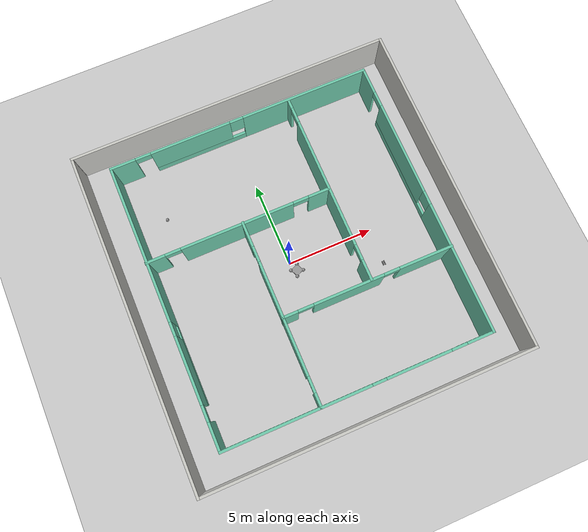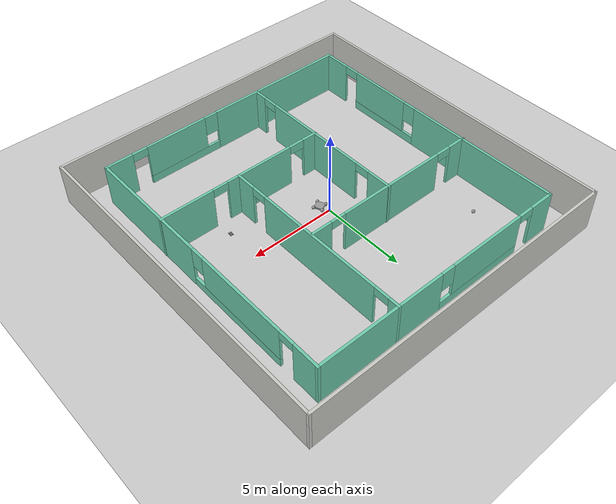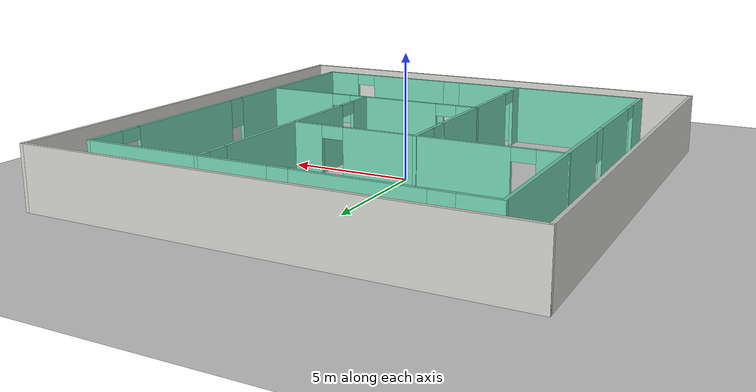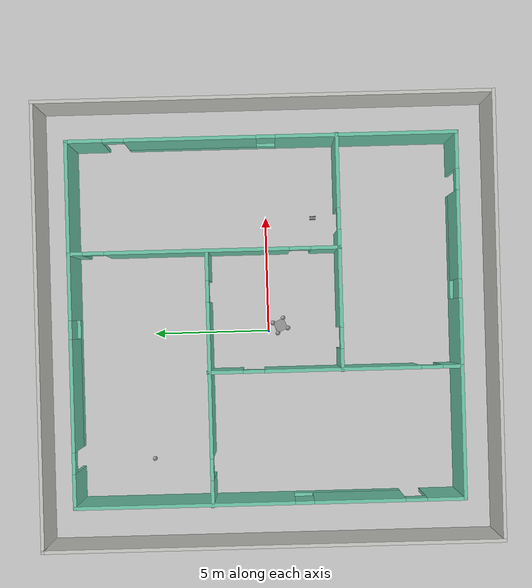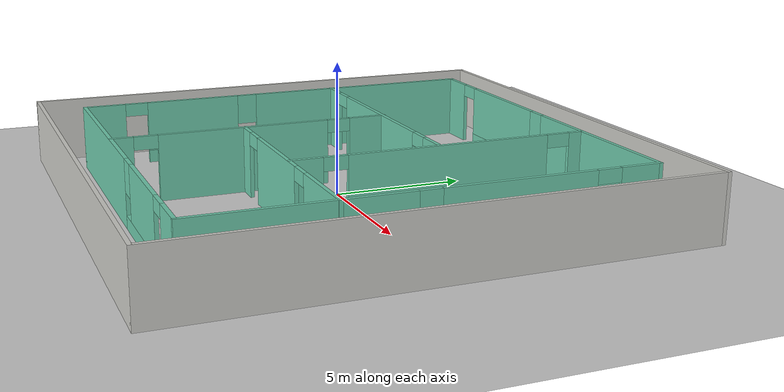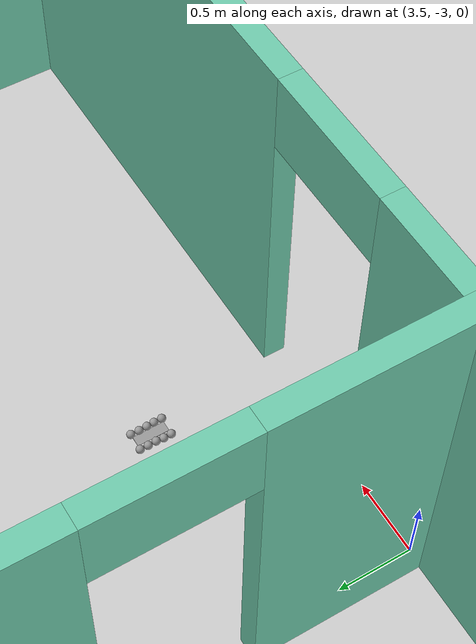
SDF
<sdf version="1.6">
 <world name="default">
  <light name="sun" type="directional">
   <pose>0 0 10 0 -0 0</pose>
   <diffuse>0.8 0.8 0.8 1</diffuse>
   <specular>0.2 0.2 0.2 1</specular>
   <attenuation>
    <range>1000</range>
    <constant>0.9</constant>
    <linear>0.01</linear>
    <quadratic>0.001</quadratic>
   </attenuation>
   <direction>-0.5 0.1 -0.9</direction>
  </light>
  <model name="ground_plane">
   <static>1</static>
   <link name="link">
    <collision name="collision">
     <geometry><plane><normal>0 0 1</normal><size>100 100</size></plane></geometry>
     <surface>
      <contact><collide_bitmask>65535</collide_bitmask></contact>
      <friction><ode><mu>100</mu><mu2>50</mu2></ode></friction>
     </surface>
    </collision>
    <visual name="visual">
     <cast_shadows>0</cast_shadows>
     <geometry><plane><normal>0 0 1</normal><size>100 100</size></plane></geometry>
     <material>
      <script><uri>file://media/materials/scripts/gazebo.material</uri><name>Gazebo/Grey</name></script>
     </material>
    </visual>
   </link>
  </model>
  <gravity>0 0 -9.8</gravity>
  <magnetic_field>6e-06 2.3e-05 -4.2e-05</magnetic_field>
  <atmosphere type="adiabatic"/>
  <physics name="default_physics" default="0" type="ode">
   <max_step_size>0.001</max_step_size>
   <real_time_factor>1</real_time_factor>
   <real_time_update_rate>1000</real_time_update_rate>
  </physics>
  <scene><ambient>0.4 0.4 0.4 1</ambient><background>0.7 0.7 0.7 1</background><shadows>1</shadows></scene>
  <audio><device>default</device></audio>
  <spherical_coordinates>
   <surface_model>EARTH_WGS84</surface_model>
   <latitude_deg>0</latitude_deg>
   <longitude_deg>0</longitude_deg>
   <elevation>0</elevation>
   <heading_deg>0</heading_deg>
  </spherical_coordinates>
  <model name="Building">
   <pose>0.43599 0.01676 0 0 -0 0</pose>
   <link name="Wall_101">
    <pose>-2.08663 -2.75527 0 0 -0 -1.5708</pose>
    <visual name="Wall_101_Visual_0">
     <pose>-4.61745 0 1.25 0 -0 0</pose>
     <geometry><box><size>1.51509 0.15 2.5</size></box></geometry>
     <material>
      <script><uri>file://media/materials/scripts/gazebo.material</uri><name>Gazebo/Grey</name></script>
      <ambient>0.435294 0.796078 0.67451 1</ambient>
     </material>
     <meta><layer>0</layer></meta>
    </visual>
    <collision name="Wall_101_Collision_0">
     <geometry><box><size>1.51509 0.15 2.5</size></box></geometry>
     <pose>-4.61745 0 1.25 0 -0 0</pose>
    </collision>
    <visual name="Wall_101_Visual_1">
     <pose>0.323003 0 1.25 0 -0 0</pose>
     <geometry><box><size>6.56583 0.15 2.5</size></box></geometry>
     <material>
      <script><uri>file://media/materials/scripts/gazebo.material</uri><name>Gazebo/Grey</name></script>
      <ambient>0.435294 0.796078 0.67451 1</ambient>
     </material>
     <meta><layer>0</layer></meta>
    </visual>
    <collision name="Wall_101_Collision_1">
     <geometry><box><size>6.56583 0.15 2.5</size></box></geometry>
     <pose>0.323003 0 1.25 0 -0 0</pose>
    </collision>
    <visual name="Wall_101_Visual_2">
     <pose>4.94046 0 1.25 0 -0 0</pose>
     <geometry><box><size>0.869084 0.15 2.5</size></box></geometry>
     <material>
      <script><uri>file://media/materials/scripts/gazebo.material</uri><name>Gazebo/Grey</name></script>
      <ambient>0.435294 0.796078 0.67451 1</ambient>
     </material>
     <meta><layer>0</layer></meta>
    </visual>
    <collision name="Wall_101_Collision_2">
     <geometry><box><size>0.869084 0.15 2.5</size></box></geometry>
     <pose>4.94046 0 1.25 0 -0 0</pose>
    </collision>
    <visual name="Wall_101_Visual_3">
     <pose>-3.40991 0 2.25 0 -0 0</pose>
     <geometry><box><size>0.9 0.15 0.5</size></box></geometry>
     <material>
      <script><uri>file://media/materials/scripts/gazebo.material</uri><name>Gazebo/Grey</name></script>
      <ambient>0.435294 0.796078 0.67451 1</ambient>
     </material>
     <meta><layer>0</layer></meta>
    </visual>
    <collision name="Wall_101_Collision_3">
     <geometry><box><size>0.9 0.15 0.5</size></box></geometry>
     <pose>-3.40991 0 2.25 0 -0 0</pose>
    </collision>
    <visual name="Wall_101_Visual_4">
     <pose>4.05592 0 2.25 0 -0 0</pose>
     <geometry><box><size>0.9 0.15 0.5</size></box></geometry>
     <material>
      <script><uri>file://media/materials/scripts/gazebo.material</uri><name>Gazebo/Grey</name></script>
      <ambient>0.435294 0.796078 0.67451 1</ambient>
     </material>
     <meta><layer>0</layer></meta>
    </visual>
    <collision name="Wall_101_Collision_4">
     <geometry><box><size>0.9 0.15 0.5</size></box></geometry>
     <pose>4.05592 0 2.25 0 -0 0</pose>
    </collision>
   </link>
   <link name="Wall_84">
    <collision name="Wall_84_Collision">
     <geometry><box><size>19.5 0.15 2.5</size></box></geometry>
     <pose>0 0 1.25 0 -0 0</pose>
    </collision>
    <visual name="Wall_84_Visual">
     <pose>0 0 1.25 0 -0 0</pose>
     <geometry><box><size>19.5 0.15 2.5</size></box></geometry>
     <material>
      <script><uri>file://media/materials/scripts/gazebo.material</uri><name>Gazebo/CeilingTiled</name></script>
      <ambient>1 1 1 1</ambient>
     </material>
     <meta><layer>0</layer></meta>
    </visual>
    <pose>-9.425 0 0 0 -0 -1.5708</pose>
   </link>
   <link name="Wall_85">
    <collision name="Wall_85_Collision">
     <geometry><box><size>19 0.15 2.5</size></box></geometry>
     <pose>0 0 1.25 0 -0 0</pose>
    </collision>
    <visual name="Wall_85_Visual">
     <pose>0 0 1.25 0 -0 0</pose>
     <geometry><box><size>19 0.15 2.5</size></box></geometry>
     <material>
      <script><uri>file://media/materials/scripts/gazebo.material</uri><name>Gazebo/CeilingTiled</name></script>
      <ambient>1 1 1 1</ambient>
     </material>
     <meta><layer>0</layer></meta>
    </visual>
    <pose>0 -9.675 0 0 -0 0</pose>
   </link>
   <link name="Wall_86">
    <collision name="Wall_86_Collision">
     <geometry><box><size>19.5 0.15 2.5</size></box></geometry>
     <pose>0 0 1.25 0 -0 0</pose>
    </collision>
    <visual name="Wall_86_Visual">
     <pose>0 0 1.25 0 -0 0</pose>
     <geometry><box><size>19.5 0.15 2.5</size></box></geometry>
     <material>
      <script><uri>file://media/materials/scripts/gazebo.material</uri><name>Gazebo/CeilingTiled</name></script>
      <ambient>1 1 1 1</ambient>
     </material>
     <meta><layer>0</layer></meta>
    </visual>
    <pose>9.425 0 0 0 -0 1.5708</pose>
   </link>
   <link name="Wall_87">
    <collision name="Wall_87_Collision">
     <geometry><box><size>19 0.15 2.5</size></box></geometry>
     <pose>0 0 1.25 0 -0 0</pose>
    </collision>
    <visual name="Wall_87_Visual">
     <pose>0 0 1.25 0 -0 0</pose>
     <geometry><box><size>19 0.15 2.5</size></box></geometry>
     <material>
      <script><uri>file://media/materials/scripts/gazebo.material</uri><name>Gazebo/CeilingTiled</name></script>
      <ambient>1 1 1 1</ambient>
     </material>
     <meta><layer>0</layer></meta>
    </visual>
    <pose>0 9.675 0 0 -0 3.14159</pose>
   </link>
   <link name="Wall_88">
    <collision name="Wall_88_Collision">
     <geometry><box><size>0.16 0.15 2.5</size></box></geometry>
     <pose>0 0 1.25 0 -0 0</pose>
    </collision>
    <visual name="Wall_88_Visual">
     <pose>0 0 1.25 0 -0 0</pose>
     <geometry><box><size>0.16 0.15 2.5</size></box></geometry>
     <material>
      <script><uri>file://media/materials/scripts/gazebo.material</uri><name>Gazebo/Grey</name></script>
      <ambient>1 1 1 1</ambient>
     </material>
     <meta><layer>0</layer></meta>
    </visual>
    <pose>-9.42 9.675 0 0 -0 0</pose>
   </link>
   <link name="Wall_90">
    <pose>-7.62558 0.103719 0 0 -0 -1.5708</pose>
    <visual name="Wall_90_Visual_0">
     <pose>-3.59802 0 1.25 0 -0 0</pose>
     <geometry><box><size>9.30396 0.15 2.5</size></box></geometry>
     <material>
      <script><uri>file://media/materials/scripts/gazebo.material</uri><name>Gazebo/Grey</name></script>
      <ambient>0.435294 0.796078 0.67451 1</ambient>
     </material>
     <meta><layer>0</layer></meta>
    </visual>
    <collision name="Wall_90_Collision_0">
     <geometry><box><size>9.30396 0.15 2.5</size></box></geometry>
     <pose>-3.59802 0 1.25 0 -0 0</pose>
    </collision>
    <visual name="Wall_90_Visual_1">
     <pose>7.40961 0 1.25 0 -0 0</pose>
     <geometry><box><size>1.68078 0.15 2.5</size></box></geometry>
     <material>
      <script><uri>file://media/materials/scripts/gazebo.material</uri><name>Gazebo/Grey</name></script>
      <ambient>0.435294 0.796078 0.67451 1</ambient>
     </material>
     <meta><layer>0</layer></meta>
    </visual>
    <collision name="Wall_90_Collision_1">
     <geometry><box><size>1.68078 0.15 2.5</size></box></geometry>
     <pose>7.40961 0 1.25 0 -0 0</pose>
    </collision>
    <visual name="Wall_90_Visual_2">
     <pose>3.36159 0 0.25 0 -0 0</pose>
     <geometry><box><size>4.61526 0.15 0.5</size></box></geometry>
     <material>
      <script><uri>file://media/materials/scripts/gazebo.material</uri><name>Gazebo/Grey</name></script>
      <ambient>0.435294 0.796078 0.67451 1</ambient>
     </material>
     <meta><layer>0</layer></meta>
    </visual>
    <collision name="Wall_90_Collision_2">
     <geometry><box><size>4.61526 0.15 0.5</size></box></geometry>
     <pose>3.36159 0 0.25 0 -0 0</pose>
    </collision>
    <visual name="Wall_90_Visual_3">
     <pose>3.76159 0 1.5 0 -0 0</pose>
     <geometry><box><size>3.81526 0.15 2</size></box></geometry>
     <material>
      <script><uri>file://media/materials/scripts/gazebo.material</uri><name>Gazebo/Grey</name></script>
      <ambient>0.435294 0.796078 0.67451 1</ambient>
     </material>
     <meta><layer>0</layer></meta>
    </visual>
    <collision name="Wall_90_Collision_3">
     <geometry><box><size>3.81526 0.15 2</size></box></geometry>
     <pose>3.76159 0 1.5 0 -0 0</pose>
    </collision>
    <visual name="Wall_90_Visual_4">
     <pose>1.45396 0 1.9 0 -0 0</pose>
     <geometry><box><size>0.8 0.15 1.2</size></box></geometry>
     <material>
      <script><uri>file://media/materials/scripts/gazebo.material</uri><name>Gazebo/Grey</name></script>
      <ambient>0.435294 0.796078 0.67451 1</ambient>
     </material>
     <meta><layer>0</layer></meta>
    </visual>
    <collision name="Wall_90_Collision_4">
     <geometry><box><size>0.8 0.15 1.2</size></box></geometry>
     <pose>1.45396 0 1.9 0 -0 0</pose>
    </collision>
    <visual name="Wall_90_Visual_5">
     <pose>6.11922 0 2.25 0 -0 0</pose>
     <geometry><box><size>0.9 0.15 0.5</size></box></geometry>
     <material>
      <script><uri>file://media/materials/scripts/gazebo.material</uri><name>Gazebo/Grey</name></script>
      <ambient>0.435294 0.796078 0.67451 1</ambient>
     </material>
     <meta><layer>0</layer></meta>
    </visual>
    <collision name="Wall_90_Collision_5">
     <geometry><box><size>0.9 0.15 0.5</size></box></geometry>
     <pose>6.11922 0 2.25 0 -0 0</pose>
    </collision>
   </link>
   <link name="Wall_91">
    <pose>0.049418 -8.07128 0 0 -0 0</pose>
    <visual name="Wall_91_Visual_0">
     <pose>-3.51293 0 1.25 0 -0 0</pose>
     <geometry><box><size>8.47414 0.15 2.5</size></box></geometry>
     <material>
      <script><uri>file://media/materials/scripts/gazebo.material</uri><name>Gazebo/Grey</name></script>
      <ambient>0.435294 0.796078 0.67451 1</ambient>
     </material>
     <meta><layer>0</layer></meta>
    </visual>
    <collision name="Wall_91_Collision_0">
     <geometry><box><size>8.47414 0.15 2.5</size></box></geometry>
     <pose>-3.51293 0 1.25 0 -0 0</pose>
    </collision>
    <visual name="Wall_91_Visual_1">
     <pose>6.94158 0 1.25 0 -0 0</pose>
     <geometry><box><size>1.61685 0.15 2.5</size></box></geometry>
     <material>
      <script><uri>file://media/materials/scripts/gazebo.material</uri><name>Gazebo/Grey</name></script>
      <ambient>0.435294 0.796078 0.67451 1</ambient>
     </material>
     <meta><layer>0</layer></meta>
    </visual>
    <collision name="Wall_91_Collision_1">
     <geometry><box><size>1.61685 0.15 2.5</size></box></geometry>
     <pose>6.94158 0 1.25 0 -0 0</pose>
    </collision>
    <visual name="Wall_91_Visual_2">
     <pose>2.97865 0 0.25 0 -0 0</pose>
     <geometry><box><size>4.50901 0.15 0.5</size></box></geometry>
     <material>
      <script><uri>file://media/materials/scripts/gazebo.material</uri><name>Gazebo/Grey</name></script>
      <ambient>0.435294 0.796078 0.67451 1</ambient>
     </material>
     <meta><layer>0</layer></meta>
    </visual>
    <collision name="Wall_91_Collision_2">
     <geometry><box><size>4.50901 0.15 0.5</size></box></geometry>
     <pose>2.97865 0 0.25 0 -0 0</pose>
    </collision>
    <visual name="Wall_91_Visual_3">
     <pose>3.37865 0 1.5 0 -0 0</pose>
     <geometry><box><size>3.70901 0.15 2</size></box></geometry>
     <material>
      <script><uri>file://media/materials/scripts/gazebo.material</uri><name>Gazebo/Grey</name></script>
      <ambient>0.435294 0.796078 0.67451 1</ambient>
     </material>
     <meta><layer>0</layer></meta>
    </visual>
    <collision name="Wall_91_Collision_3">
     <geometry><box><size>3.70901 0.15 2</size></box></geometry>
     <pose>3.37865 0 1.5 0 -0 0</pose>
    </collision>
    <visual name="Wall_91_Visual_4">
     <pose>1.12414 0 1.9 0 -0 0</pose>
     <geometry><box><size>0.8 0.15 1.2</size></box></geometry>
     <material>
      <script><uri>file://media/materials/scripts/gazebo.material</uri><name>Gazebo/Grey</name></script>
      <ambient>0.435294 0.796078 0.67451 1</ambient>
     </material>
     <meta><layer>0</layer></meta>
    </visual>
    <collision name="Wall_91_Collision_4">
     <geometry><box><size>0.8 0.15 1.2</size></box></geometry>
     <pose>1.12414 0 1.9 0 -0 0</pose>
    </collision>
    <visual name="Wall_91_Visual_5">
     <pose>5.68315 0 2.25 0 -0 0</pose>
     <geometry><box><size>0.9 0.15 0.5</size></box></geometry>
     <material>
      <script><uri>file://media/materials/scripts/gazebo.material</uri><name>Gazebo/Grey</name></script>
      <ambient>0.435294 0.796078 0.67451 1</ambient>
     </material>
     <meta><layer>0</layer></meta>
    </visual>
    <collision name="Wall_91_Collision_5">
     <geometry><box><size>0.9 0.15 0.5</size></box></geometry>
     <pose>5.68315 0 2.25 0 -0 0</pose>
    </collision>
   </link>
   <link name="Wall_92">
    <pose>7.72442 0.103719 0 0 -0 1.5708</pose>
    <visual name="Wall_92_Visual_0">
     <pose>-4.42448 0 1.25 0 -0 0</pose>
     <geometry><box><size>7.65104 0.15 2.5</size></box></geometry>
     <material>
      <script><uri>file://media/materials/scripts/gazebo.material</uri><name>Gazebo/Grey</name></script>
      <ambient>0.435294 0.796078 0.67451 1</ambient>
     </material>
     <meta><layer>0</layer></meta>
    </visual>
    <collision name="Wall_92_Collision_0">
     <geometry><box><size>7.65104 0.15 2.5</size></box></geometry>
     <pose>-4.42448 0 1.25 0 -0 0</pose>
    </collision>
    <visual name="Wall_92_Visual_1">
     <pose>7.45345 0 1.25 0 -0 0</pose>
     <geometry><box><size>1.5931 0.15 2.5</size></box></geometry>
     <material>
      <script><uri>file://media/materials/scripts/gazebo.material</uri><name>Gazebo/Grey</name></script>
      <ambient>0.435294 0.796078 0.67451 1</ambient>
     </material>
     <meta><layer>0</layer></meta>
    </visual>
    <collision name="Wall_92_Collision_1">
     <geometry><box><size>1.5931 0.15 2.5</size></box></geometry>
     <pose>7.45345 0 1.25 0 -0 0</pose>
    </collision>
    <visual name="Wall_92_Visual_2">
     <pose>2.57897 0 0.25 0 -0 0</pose>
     <geometry><box><size>6.35586 0.15 0.5</size></box></geometry>
     <material>
      <script><uri>file://media/materials/scripts/gazebo.material</uri><name>Gazebo/Grey</name></script>
      <ambient>0.435294 0.796078 0.67451 1</ambient>
     </material>
     <meta><layer>0</layer></meta>
    </visual>
    <collision name="Wall_92_Collision_2">
     <geometry><box><size>6.35586 0.15 0.5</size></box></geometry>
     <pose>2.57897 0 0.25 0 -0 0</pose>
    </collision>
    <visual name="Wall_92_Visual_3">
     <pose>2.97897 0 1.5 0 -0 0</pose>
     <geometry><box><size>5.55586 0.15 2</size></box></geometry>
     <material>
      <script><uri>file://media/materials/scripts/gazebo.material</uri><name>Gazebo/Grey</name></script>
      <ambient>0.435294 0.796078 0.67451 1</ambient>
     </material>
     <meta><layer>0</layer></meta>
    </visual>
    <collision name="Wall_92_Collision_3">
     <geometry><box><size>5.55586 0.15 2</size></box></geometry>
     <pose>2.97897 0 1.5 0 -0 0</pose>
    </collision>
    <visual name="Wall_92_Visual_4">
     <pose>-0.198964 0 1.9 0 -0 0</pose>
     <geometry><box><size>0.8 0.15 1.2</size></box></geometry>
     <material>
      <script><uri>file://media/materials/scripts/gazebo.material</uri><name>Gazebo/Grey</name></script>
      <ambient>0.435294 0.796078 0.67451 1</ambient>
     </material>
     <meta><layer>0</layer></meta>
    </visual>
    <collision name="Wall_92_Collision_4">
     <geometry><box><size>0.8 0.15 1.2</size></box></geometry>
     <pose>-0.198964 0 1.9 0 -0 0</pose>
    </collision>
    <visual name="Wall_92_Visual_5">
     <pose>6.2069 0 2.25 0 -0 0</pose>
     <geometry><box><size>0.9 0.15 0.5</size></box></geometry>
     <material>
      <script><uri>file://media/materials/scripts/gazebo.material</uri><name>Gazebo/Grey</name></script>
      <ambient>0.435294 0.796078 0.67451 1</ambient>
     </material>
     <meta><layer>0</layer></meta>
    </visual>
    <collision name="Wall_92_Collision_5">
     <geometry><box><size>0.9 0.15 0.5</size></box></geometry>
     <pose>6.2069 0 2.25 0 -0 0</pose>
    </collision>
   </link>
   <link name="Wall_93">
    <pose>0.049418 8.27872 0 0 -0 3.14159</pose>
    <visual name="Wall_93_Visual_0">
     <pose>-3.97565 0 1.25 0 -0 0</pose>
     <geometry><box><size>7.5487 0.15 2.5</size></box></geometry>
     <material>
      <script><uri>file://media/materials/scripts/gazebo.material</uri><name>Gazebo/Grey</name></script>
      <ambient>0.435294 0.796078 0.67451 1</ambient>
     </material>
     <meta><layer>0</layer></meta>
    </visual>
    <collision name="Wall_93_Collision_0">
     <geometry><box><size>7.5487 0.15 2.5</size></box></geometry>
     <pose>-3.97565 0 1.25 0 -0 0</pose>
    </collision>
    <visual name="Wall_93_Visual_1">
     <pose>6.99241 0 1.25 0 -0 0</pose>
     <geometry><box><size>1.51518 0.15 2.5</size></box></geometry>
     <material>
      <script><uri>file://media/materials/scripts/gazebo.material</uri><name>Gazebo/Grey</name></script>
      <ambient>0.435294 0.796078 0.67451 1</ambient>
     </material>
     <meta><layer>0</layer></meta>
    </visual>
    <collision name="Wall_93_Collision_1">
     <geometry><box><size>1.51518 0.15 2.5</size></box></geometry>
     <pose>6.99241 0 1.25 0 -0 0</pose>
    </collision>
    <visual name="Wall_93_Visual_2">
     <pose>2.56676 0 0.25 0 -0 0</pose>
     <geometry><box><size>5.53612 0.15 0.5</size></box></geometry>
     <material>
      <script><uri>file://media/materials/scripts/gazebo.material</uri><name>Gazebo/Grey</name></script>
      <ambient>0.435294 0.796078 0.67451 1</ambient>
     </material>
     <meta><layer>0</layer></meta>
    </visual>
    <collision name="Wall_93_Collision_2">
     <geometry><box><size>5.53612 0.15 0.5</size></box></geometry>
     <pose>2.56676 0 0.25 0 -0 0</pose>
    </collision>
    <visual name="Wall_93_Visual_3">
     <pose>2.96676 0 1.5 0 -0 0</pose>
     <geometry><box><size>4.73612 0.15 2</size></box></geometry>
     <material>
      <script><uri>file://media/materials/scripts/gazebo.material</uri><name>Gazebo/Grey</name></script>
      <ambient>0.435294 0.796078 0.67451 1</ambient>
     </material>
     <meta><layer>0</layer></meta>
    </visual>
    <collision name="Wall_93_Collision_3">
     <geometry><box><size>4.73612 0.15 2</size></box></geometry>
     <pose>2.96676 0 1.5 0 -0 0</pose>
    </collision>
    <visual name="Wall_93_Visual_4">
     <pose>0.198698 0 1.9 0 -0 0</pose>
     <geometry><box><size>0.8 0.15 1.2</size></box></geometry>
     <material>
      <script><uri>file://media/materials/scripts/gazebo.material</uri><name>Gazebo/Grey</name></script>
      <ambient>0.435294 0.796078 0.67451 1</ambient>
     </material>
     <meta><layer>0</layer></meta>
    </visual>
    <collision name="Wall_93_Collision_4">
     <geometry><box><size>0.8 0.15 1.2</size></box></geometry>
     <pose>0.198698 0 1.9 0 -0 0</pose>
    </collision>
    <visual name="Wall_93_Visual_5">
     <pose>5.78482 0 2.25 0 -0 0</pose>
     <geometry><box><size>0.9 0.15 0.5</size></box></geometry>
     <material>
      <script><uri>file://media/materials/scripts/gazebo.material</uri><name>Gazebo/Grey</name></script>
      <ambient>0.435294 0.796078 0.67451 1</ambient>
     </material>
     <meta><layer>0</layer></meta>
    </visual>
    <collision name="Wall_93_Collision_5">
     <geometry><box><size>0.9 0.15 0.5</size></box></geometry>
     <pose>5.78482 0 2.25 0 -0 0</pose>
    </collision>
   </link>
   <link name="Wall_95">
    <pose>-2.36459 2.50573 0 0 -0 0</pose>
    <visual name="Wall_95_Visual_0">
     <pose>-4.80187 0 1.25 0 -0 0</pose>
     <geometry><box><size>1.14626 0.15 2.5</size></box></geometry>
     <material>
      <script><uri>file://media/materials/scripts/gazebo.material</uri><name>Gazebo/Grey</name></script>
      <ambient>0.435294 0.796078 0.67451 1</ambient>
     </material>
     <meta><layer>0</layer></meta>
    </visual>
    <collision name="Wall_95_Collision_0">
     <geometry><box><size>1.14626 0.15 2.5</size></box></geometry>
     <pose>-4.80187 0 1.25 0 -0 0</pose>
    </collision>
    <visual name="Wall_95_Visual_1">
     <pose>-0.044669 0 1.25 0 -0 0</pose>
     <geometry><box><size>6.56814 0.15 2.5</size></box></geometry>
     <material>
      <script><uri>file://media/materials/scripts/gazebo.material</uri><name>Gazebo/Grey</name></script>
      <ambient>0.435294 0.796078 0.67451 1</ambient>
     </material>
     <meta><layer>0</layer></meta>
    </visual>
    <collision name="Wall_95_Collision_1">
     <geometry><box><size>6.56814 0.15 2.5</size></box></geometry>
     <pose>-0.044669 0 1.25 0 -0 0</pose>
    </collision>
    <visual name="Wall_95_Visual_2">
     <pose>4.7572 0 1.25 0 -0 0</pose>
     <geometry><box><size>1.2356 0.15 2.5</size></box></geometry>
     <material>
      <script><uri>file://media/materials/scripts/gazebo.material</uri><name>Gazebo/Grey</name></script>
      <ambient>0.435294 0.796078 0.67451 1</ambient>
     </material>
     <meta><layer>0</layer></meta>
    </visual>
    <collision name="Wall_95_Collision_2">
     <geometry><box><size>1.2356 0.15 2.5</size></box></geometry>
     <pose>4.7572 0 1.25 0 -0 0</pose>
    </collision>
    <visual name="Wall_95_Visual_3">
     <pose>-3.77874 0 2.25 0 -0 0</pose>
     <geometry><box><size>0.9 0.15 0.5</size></box></geometry>
     <material>
      <script><uri>file://media/materials/scripts/gazebo.material</uri><name>Gazebo/Grey</name></script>
      <ambient>0.435294 0.796078 0.67451 1</ambient>
     </material>
     <meta><layer>0</layer></meta>
    </visual>
    <collision name="Wall_95_Collision_3">
     <geometry><box><size>0.9 0.15 0.5</size></box></geometry>
     <pose>-3.77874 0 2.25 0 -0 0</pose>
    </collision>
    <visual name="Wall_95_Visual_4">
     <pose>3.6894 0 2.25 0 -0 0</pose>
     <geometry><box><size>0.9 0.15 0.5</size></box></geometry>
     <material>
      <script><uri>file://media/materials/scripts/gazebo.material</uri><name>Gazebo/Grey</name></script>
      <ambient>0.435294 0.796078 0.67451 1</ambient>
     </material>
     <meta><layer>0</layer></meta>
    </visual>
    <collision name="Wall_95_Collision_4">
     <geometry><box><size>0.9 0.15 0.5</size></box></geometry>
     <pose>3.6894 0 2.25 0 -0 0</pose>
    </collision>
   </link>
   <link name="Wall_97">
    <pose>3.02325 2.60372 0 0 -0 -1.5708</pose>
    <visual name="Wall_97_Visual_0">
     <pose>-5.42153 0 1.25 0 -0 0</pose>
     <geometry><box><size>0.656941 0.15 2.5</size></box></geometry>
     <material>
      <script><uri>file://media/materials/scripts/gazebo.material</uri><name>Gazebo/Grey</name></script>
      <ambient>0.435294 0.796078 0.67451 1</ambient>
     </material>
     <meta><layer>0</layer></meta>
    </visual>
    <collision name="Wall_97_Collision_0">
     <geometry><box><size>0.656941 0.15 2.5</size></box></geometry>
     <pose>-5.42153 0 1.25 0 -0 0</pose>
    </collision>
    <visual name="Wall_97_Visual_1">
     <pose>-0.309795 0 1.25 0 -0 0</pose>
     <geometry><box><size>7.76653 0.15 2.5</size></box></geometry>
     <material>
      <script><uri>file://media/materials/scripts/gazebo.material</uri><name>Gazebo/Grey</name></script>
      <ambient>0.435294 0.796078 0.67451 1</ambient>
     </material>
     <meta><layer>0</layer></meta>
    </visual>
    <collision name="Wall_97_Collision_1">
     <geometry><box><size>7.76653 0.15 2.5</size></box></geometry>
     <pose>-0.309795 0 1.25 0 -0 0</pose>
    </collision>
    <visual name="Wall_97_Visual_2">
     <pose>5.11174 0 1.25 0 -0 0</pose>
     <geometry><box><size>1.27653 0.15 2.5</size></box></geometry>
     <material>
      <script><uri>file://media/materials/scripts/gazebo.material</uri><name>Gazebo/Grey</name></script>
      <ambient>0.435294 0.796078 0.67451 1</ambient>
     </material>
     <meta><layer>0</layer></meta>
    </visual>
    <collision name="Wall_97_Collision_2">
     <geometry><box><size>1.27653 0.15 2.5</size></box></geometry>
     <pose>5.11174 0 1.25 0 -0 0</pose>
    </collision>
    <visual name="Wall_97_Visual_3">
     <pose>-4.64306 0 2.25 0 -0 0</pose>
     <geometry><box><size>0.9 0.15 0.5</size></box></geometry>
     <material>
      <script><uri>file://media/materials/scripts/gazebo.material</uri><name>Gazebo/Grey</name></script>
      <ambient>0.435294 0.796078 0.67451 1</ambient>
     </material>
     <meta><layer>0</layer></meta>
    </visual>
    <collision name="Wall_97_Collision_3">
     <geometry><box><size>0.9 0.15 0.5</size></box></geometry>
     <pose>-4.64306 0 2.25 0 -0 0</pose>
    </collision>
    <visual name="Wall_97_Visual_4">
     <pose>4.02347 0 2.25 0 -0 0</pose>
     <geometry><box><size>0.9 0.15 0.5</size></box></geometry>
     <material>
      <script><uri>file://media/materials/scripts/gazebo.material</uri><name>Gazebo/Grey</name></script>
      <ambient>0.435294 0.796078 0.67451 1</ambient>
     </material>
     <meta><layer>0</layer></meta>
    </visual>
    <collision name="Wall_97_Collision_4">
     <geometry><box><size>0.9 0.15 0.5</size></box></geometry>
     <pose>4.02347 0 2.25 0 -0 0</pose>
    </collision>
   </link>
   <link name="Wall_99">
    <pose>2.81806 -3.07223 0 0 -0 3.14159</pose>
    <visual name="Wall_99_Visual_0">
     <pose>-3.42162 0 1.25 0 -0 0</pose>
     <geometry><box><size>3.15675 0.15 2.5</size></box></geometry>
     <material>
      <script><uri>file://media/materials/scripts/gazebo.material</uri><name>Gazebo/Grey</name></script>
      <ambient>0.435294 0.796078 0.67451 1</ambient>
     </material>
     <meta><layer>0</layer></meta>
    </visual>
    <collision name="Wall_99_Collision_0">
     <geometry><box><size>3.15675 0.15 2.5</size></box></geometry>
     <pose>-3.42162 0 1.25 0 -0 0</pose>
    </collision>
    <visual name="Wall_99_Visual_1">
     <pose>1.10318 0 1.25 0 -0 0</pose>
     <geometry><box><size>4.09286 0.15 2.5</size></box></geometry>
     <material>
      <script><uri>file://media/materials/scripts/gazebo.material</uri><name>Gazebo/Grey</name></script>
      <ambient>0.435294 0.796078 0.67451 1</ambient>
     </material>
     <meta><layer>0</layer></meta>
    </visual>
    <collision name="Wall_99_Collision_1">
     <geometry><box><size>4.09286 0.15 2.5</size></box></geometry>
     <pose>1.10318 0 1.25 0 -0 0</pose>
    </collision>
    <visual name="Wall_99_Visual_2">
     <pose>4.52481 0 1.25 0 -0 0</pose>
     <geometry><box><size>0.950387 0.15 2.5</size></box></geometry>
     <material>
      <script><uri>file://media/materials/scripts/gazebo.material</uri><name>Gazebo/Grey</name></script>
      <ambient>0.435294 0.796078 0.67451 1</ambient>
     </material>
     <meta><layer>0</layer></meta>
    </visual>
    <collision name="Wall_99_Collision_2">
     <geometry><box><size>0.950387 0.15 2.5</size></box></geometry>
     <pose>4.52481 0 1.25 0 -0 0</pose>
    </collision>
    <visual name="Wall_99_Visual_3">
     <pose>-1.39325 0 2.25 0 -0 0</pose>
     <geometry><box><size>0.9 0.15 0.5</size></box></geometry>
     <material>
      <script><uri>file://media/materials/scripts/gazebo.material</uri><name>Gazebo/Grey</name></script>
      <ambient>0.435294 0.796078 0.67451 1</ambient>
     </material>
     <meta><layer>0</layer></meta>
    </visual>
    <collision name="Wall_99_Collision_3">
     <geometry><box><size>0.9 0.15 0.5</size></box></geometry>
     <pose>-1.39325 0 2.25 0 -0 0</pose>
    </collision>
    <visual name="Wall_99_Visual_4">
     <pose>3.59961 0 2.25 0 -0 0</pose>
     <geometry><box><size>0.9 0.15 0.5</size></box></geometry>
     <material>
      <script><uri>file://media/materials/scripts/gazebo.material</uri><name>Gazebo/Grey</name></script>
      <ambient>0.435294 0.796078 0.67451 1</ambient>
     </material>
     <meta><layer>0</layer></meta>
    </visual>
    <collision name="Wall_99_Collision_4">
     <geometry><box><size>0.9 0.15 0.5</size></box></geometry>
     <pose>3.59961 0 2.25 0 -0 0</pose>
    </collision>
   </link>
   <static>1</static>
  </model>
  <model name="Robot2">
   <model name="Untitled">
    <link name="link_1">
     <inertial>
      <mass>7.02917e-05</mass>
      <inertia>
       <ixx>2.83738e-07</ixx>
       <ixy>0</ixy>
       <ixz>0</ixz>
       <iyy>2.92102e-08</iyy>
       <iyz>0</iyz>
       <izz>3.12703e-07</izz>
      </inertia>
     </inertial>
     <pose>0.001933 0.001386 -0.002717 0 -0 0</pose>
     <visual name="visual">
      <geometry><box><size>0.070469 0.220041 0.004569</size></box></geometry>
      <material>
       <lighting>1</lighting>
       <script><uri>file://media/materials/scripts/gazebo.material</uri><name>Gazebo/Grey</name></script>
      </material>
     </visual>
     <collision name="collision">
      <geometry><box><size>0.070469 0.220041 0.004569</size></box></geometry>
      <surface>
       <friction>
        <ode><mu>1</mu><mu2>1</mu2><fdir1>0 0 0</fdir1><slip1>0</slip1><slip2>0</slip2></ode>
        <torsional>
         <coefficient>1</coefficient>
         <patch_radius>0</patch_radius>
         <surface_radius>0</surface_radius>
         <use_patch_radius>1</use_patch_radius>
         <ode><slip>0</slip></ode>
        </torsional>
       </friction>
       <bounce><restitution_coefficient>0</restitution_coefficient><threshold>1e+06</threshold></bounce>
       <contact>
        <collide_without_contact>0</collide_without_contact>
        <collide_without_contact_bitmask>1</collide_without_contact_bitmask>
        <collide_bitmask>1</collide_bitmask>
        <ode>
         <soft_cfm>0</soft_cfm>
         <soft_erp>0.2</soft_erp>
         <kp>1e+13</kp>
         <kd>1</kd>
         <max_vel>0.01</max_vel>
         <min_depth>0</min_depth>
        </ode>
        <bullet>
         <split_impulse>1</split_impulse>
         <split_impulse_penetration_threshold>-0.01</split_impulse_penetration_threshold>
         <soft_cfm>0</soft_cfm>
         <soft_erp>0.2</soft_erp>
         <kp>1e+13</kp>
         <kd>1</kd>
        </bullet>
       </contact>
      </surface>
     </collision>
    </link>
    <link name="link_2">
     <inertial>
      <mass>0.000176069</mass>
      <inertia>
       <ixx>5.52942e-08</ixx>
       <ixy>0</ixy>
       <ixz>0</ixz>
       <iyy>5.52942e-08</iyy>
       <iyz>0</iyz>
       <izz>5.52942e-08</izz>
      </inertia>
     </inertial>
     <pose>0.061204 -0.003251 0.000272 0 -0 0</pose>
     <visual name="visual">
      <geometry><sphere><radius>0.02802</radius></sphere></geometry>
      <material>
       <lighting>1</lighting>
       <script><uri>file://media/materials/scripts/gazebo.material</uri><name>Gazebo/Grey</name></script>
      </material>
     </visual>
     <collision name="collision">
      <geometry><sphere><radius>0.02802</radius></sphere></geometry>
      <surface>
       <friction>
        <ode><mu>1</mu><mu2>1</mu2><fdir1>0 0 0</fdir1><slip1>0</slip1><slip2>0</slip2></ode>
        <torsional>
         <coefficient>1</coefficient>
         <patch_radius>0</patch_radius>
         <surface_radius>0</surface_radius>
         <use_patch_radius>1</use_patch_radius>
         <ode><slip>0</slip></ode>
        </torsional>
       </friction>
       <bounce><restitution_coefficient>0</restitution_coefficient><threshold>1e+06</threshold></bounce>
       <contact>
        <collide_without_contact>0</collide_without_contact>
        <collide_without_contact_bitmask>1</collide_without_contact_bitmask>
        <collide_bitmask>1</collide_bitmask>
        <ode>
         <soft_cfm>0</soft_cfm>
         <soft_erp>0.2</soft_erp>
         <kp>1e+13</kp>
         <kd>1</kd>
         <max_vel>0.01</max_vel>
         <min_depth>0</min_depth>
        </ode>
        <bullet>
         <split_impulse>1</split_impulse>
         <split_impulse_penetration_threshold>-0.01</split_impulse_penetration_threshold>
         <soft_cfm>0</soft_cfm>
         <soft_erp>0.2</soft_erp>
         <kp>1e+13</kp>
         <kd>1</kd>
        </bullet>
       </contact>
      </surface>
     </collision>
    </link>
    <link name="link_2_clone">
     <inertial>
      <mass>0.000176069</mass>
      <inertia>
       <ixx>5.52942e-08</ixx>
       <ixy>0</ixy>
       <ixz>0</ixz>
       <iyy>5.52942e-08</iyy>
       <iyz>0</iyz>
       <izz>5.52942e-08</izz>
      </inertia>
     </inertial>
     <pose>-0.060183 -0.001647 0.000272 0 -0 0</pose>
     <visual name="visual">
      <geometry><sphere><radius>0.02802</radius></sphere></geometry>
      <material>
       <lighting>1</lighting>
       <script><uri>file://media/materials/scripts/gazebo.material</uri><name>Gazebo/Grey</name></script>
       <shader type="pixel"/>
      </material>
     </visual>
     <collision name="collision">
      <geometry><sphere><radius>0.02802</radius></sphere></geometry>
      <surface>
       <friction>
        <ode><mu>1</mu><mu2>1</mu2><fdir1>0 0 0</fdir1><slip1>0</slip1><slip2>0</slip2></ode>
        <torsional>
         <coefficient>1</coefficient>
         <patch_radius>0</patch_radius>
         <surface_radius>0</surface_radius>
         <use_patch_radius>1</use_patch_radius>
         <ode><slip>0</slip></ode>
        </torsional>
       </friction>
       <bounce><restitution_coefficient>0</restitution_coefficient><threshold>1e+06</threshold></bounce>
       <contact>
        <collide_without_contact>0</collide_without_contact>
        <collide_without_contact_bitmask>1</collide_without_contact_bitmask>
        <collide_bitmask>1</collide_bitmask>
        <ode>
         <soft_cfm>0</soft_cfm>
         <soft_erp>0.2</soft_erp>
         <kp>1e+13</kp>
         <kd>1</kd>
         <max_vel>0.01</max_vel>
         <min_depth>0</min_depth>
        </ode>
        <bullet>
         <split_impulse>1</split_impulse>
         <split_impulse_penetration_threshold>-0.01</split_impulse_penetration_threshold>
         <soft_cfm>0</soft_cfm>
         <soft_erp>0.2</soft_erp>
         <kp>1e+13</kp>
         <kd>1</kd>
        </bullet>
       </contact>
      </surface>
     </collision>
    </link>
    <link name="link_2_clone_0">
     <inertial>
      <mass>0.000176069</mass>
      <inertia>
       <ixx>5.52942e-08</ixx>
       <ixy>0</ixy>
       <ixz>0</ixz>
       <iyy>5.52942e-08</iyy>
       <iyz>0</iyz>
       <izz>5.52942e-08</izz>
      </inertia>
     </inertial>
     <pose>0.063912 -0.055099 0.000272 0 -0 0</pose>
     <visual name="visual">
      <geometry><sphere><radius>0.02802</radius></sphere></geometry>
      <material>
       <lighting>1</lighting>
       <script><uri>file://media/materials/scripts/gazebo.material</uri><name>Gazebo/Grey</name></script>
       <shader type="pixel"/>
      </material>
     </visual>
     <collision name="collision">
      <geometry><sphere><radius>0.02802</radius></sphere></geometry>
      <surface>
       <friction>
        <ode><mu>1</mu><mu2>1</mu2><fdir1>0 0 0</fdir1><slip1>0</slip1><slip2>0</slip2></ode>
        <torsional>
         <coefficient>1</coefficient>
         <patch_radius>0</patch_radius>
         <surface_radius>0</surface_radius>
         <use_patch_radius>1</use_patch_radius>
         <ode><slip>0</slip></ode>
        </torsional>
       </friction>
       <bounce><restitution_coefficient>0</restitution_coefficient><threshold>1e+06</threshold></bounce>
       <contact>
        <collide_without_contact>0</collide_without_contact>
        <collide_without_contact_bitmask>1</collide_without_contact_bitmask>
        <collide_bitmask>1</collide_bitmask>
        <ode>
         <soft_cfm>0</soft_cfm>
         <soft_erp>0.2</soft_erp>
         <kp>1e+13</kp>
         <kd>1</kd>
         <max_vel>0.01</max_vel>
         <min_depth>0</min_depth>
        </ode>
        <bullet>
         <split_impulse>1</split_impulse>
         <split_impulse_penetration_threshold>-0.01</split_impulse_penetration_threshold>
         <soft_cfm>0</soft_cfm>
         <soft_erp>0.2</soft_erp>
         <kp>1e+13</kp>
         <kd>1</kd>
        </bullet>
       </contact>
      </surface>
     </collision>
    </link>
    <link name="link_2_clone_1">
     <inertial>
      <mass>0.000176069</mass>
      <inertia>
       <ixx>5.52942e-08</ixx>
       <ixy>0</ixy>
       <ixz>0</ixz>
       <iyy>5.52942e-08</iyy>
       <iyz>0</iyz>
       <izz>5.52942e-08</izz>
      </inertia>
     </inertial>
     <pose>0.05895 0.052825 0.000272 0 -0 0</pose>
     <visual name="visual">
      <geometry><sphere><radius>0.02802</radius></sphere></geometry>
      <material>
       <lighting>1</lighting>
       <script><uri>file://media/materials/scripts/gazebo.material</uri><name>Gazebo/Grey</name></script>
       <shader type="pixel"/>
      </material>
     </visual>
     <collision name="collision">
      <geometry><sphere><radius>0.02802</radius></sphere></geometry>
      <surface>
       <friction>
        <ode><mu>1</mu><mu2>1</mu2><fdir1>0 0 0</fdir1><slip1>0</slip1><slip2>0</slip2></ode>
        <torsional>
         <coefficient>1</coefficient>
         <patch_radius>0</patch_radius>
         <surface_radius>0</surface_radius>
         <use_patch_radius>1</use_patch_radius>
         <ode><slip>0</slip></ode>
        </torsional>
       </friction>
       <bounce><restitution_coefficient>0</restitution_coefficient><threshold>1e+06</threshold></bounce>
       <contact>
        <collide_without_contact>0</collide_without_contact>
        <collide_without_contact_bitmask>1</collide_without_contact_bitmask>
        <collide_bitmask>1</collide_bitmask>
        <ode>
         <soft_cfm>0</soft_cfm>
         <soft_erp>0.2</soft_erp>
         <kp>1e+13</kp>
         <kd>1</kd>
         <max_vel>0.01</max_vel>
         <min_depth>0</min_depth>
        </ode>
        <bullet>
         <split_impulse>1</split_impulse>
         <split_impulse_penetration_threshold>-0.01</split_impulse_penetration_threshold>
         <soft_cfm>0</soft_cfm>
         <soft_erp>0.2</soft_erp>
         <kp>1e+13</kp>
         <kd>1</kd>
        </bullet>
       </contact>
      </surface>
     </collision>
    </link>
    <link name="link_2_clone_2">
     <inertial>
      <mass>0.000176069</mass>
      <inertia>
       <ixx>5.52942e-08</ixx>
       <ixy>0</ixy>
       <ixz>0</ixz>
       <iyy>5.52942e-08</iyy>
       <iyz>0</iyz>
       <izz>5.52942e-08</izz>
      </inertia>
     </inertial>
     <pose>-0.06227 0.055125 0.000272 0 -0 0</pose>
     <visual name="visual">
      <geometry><sphere><radius>0.02802</radius></sphere></geometry>
      <material>
       <lighting>1</lighting>
       <script><uri>file://media/materials/scripts/gazebo.material</uri><name>Gazebo/Grey</name></script>
       <shader type="pixel"/>
      </material>
     </visual>
     <collision name="collision">
      <geometry><sphere><radius>0.02802</radius></sphere></geometry>
      <surface>
       <friction>
        <ode><mu>1</mu><mu2>1</mu2><fdir1>0 0 0</fdir1><slip1>0</slip1><slip2>0</slip2></ode>
        <torsional>
         <coefficient>1</coefficient>
         <patch_radius>0</patch_radius>
         <surface_radius>0</surface_radius>
         <use_patch_radius>1</use_patch_radius>
         <ode><slip>0</slip></ode>
        </torsional>
       </friction>
       <bounce><restitution_coefficient>0</restitution_coefficient><threshold>1e+06</threshold></bounce>
       <contact>
        <collide_without_contact>0</collide_without_contact>
        <collide_without_contact_bitmask>1</collide_without_contact_bitmask>
        <collide_bitmask>1</collide_bitmask>
        <ode>
         <soft_cfm>0</soft_cfm>
         <soft_erp>0.2</soft_erp>
         <kp>1e+13</kp>
         <kd>1</kd>
         <max_vel>0.01</max_vel>
         <min_depth>0</min_depth>
        </ode>
        <bullet>
         <split_impulse>1</split_impulse>
         <split_impulse_penetration_threshold>-0.01</split_impulse_penetration_threshold>
         <soft_cfm>0</soft_cfm>
         <soft_erp>0.2</soft_erp>
         <kp>1e+13</kp>
         <kd>1</kd>
        </bullet>
       </contact>
      </surface>
     </collision>
    </link>
    <link name="link_2_clone_3">
     <inertial>
      <mass>0.000176069</mass>
      <inertia>
       <ixx>5.52942e-08</ixx>
       <ixy>0</ixy>
       <ixz>0</ixz>
       <iyy>5.52942e-08</iyy>
       <iyz>0</iyz>
       <izz>5.52942e-08</izz>
      </inertia>
     </inertial>
     <pose>-0.064413 -0.052925 0.000272 0 -0 0</pose>
     <visual name="visual">
      <geometry><sphere><radius>0.02802</radius></sphere></geometry>
      <material>
       <lighting>1</lighting>
       <script><uri>file://media/materials/scripts/gazebo.material</uri><name>Gazebo/Grey</name></script>
       <shader type="pixel"/>
      </material>
     </visual>
     <collision name="collision">
      <geometry><sphere><radius>0.02802</radius></sphere></geometry>
      <surface>
       <friction>
        <ode><mu>1</mu><mu2>1</mu2><fdir1>0 0 0</fdir1><slip1>0</slip1><slip2>0</slip2></ode>
        <torsional>
         <coefficient>1</coefficient>
         <patch_radius>0</patch_radius>
         <surface_radius>0</surface_radius>
         <use_patch_radius>1</use_patch_radius>
         <ode><slip>0</slip></ode>
        </torsional>
       </friction>
       <bounce><restitution_coefficient>0</restitution_coefficient><threshold>1e+06</threshold></bounce>
       <contact>
        <collide_without_contact>0</collide_without_contact>
        <collide_without_contact_bitmask>1</collide_without_contact_bitmask>
        <collide_bitmask>1</collide_bitmask>
        <ode>
         <soft_cfm>0</soft_cfm>
         <soft_erp>0.2</soft_erp>
         <kp>1e+13</kp>
         <kd>1</kd>
         <max_vel>0.01</max_vel>
         <min_depth>0</min_depth>
        </ode>
        <bullet>
         <split_impulse>1</split_impulse>
         <split_impulse_penetration_threshold>-0.01</split_impulse_penetration_threshold>
         <soft_cfm>0</soft_cfm>
         <soft_erp>0.2</soft_erp>
         <kp>1e+13</kp>
         <kd>1</kd>
        </bullet>
       </contact>
      </surface>
     </collision>
    </link>
    <link name="link_2_clone_4">
     <inertial>
      <mass>0.000176069</mass>
      <inertia>
       <ixx>5.52942e-08</ixx>
       <ixy>0</ixy>
       <ixz>0</ixz>
       <iyy>5.52942e-08</iyy>
       <iyz>0</iyz>
       <izz>5.52942e-08</izz>
      </inertia>
     </inertial>
     <pose>-0.062342 -0.107469 0.000272 0 -0 0</pose>
     <visual name="visual">
      <geometry><sphere><radius>0.02802</radius></sphere></geometry>
      <material>
       <lighting>1</lighting>
       <script><uri>file://media/materials/scripts/gazebo.material</uri><name>Gazebo/Grey</name></script>
       <shader type="pixel"/>
      </material>
     </visual>
     <collision name="collision">
      <geometry><sphere><radius>0.02802</radius></sphere></geometry>
      <surface>
       <friction>
        <ode><mu>1</mu><mu2>1</mu2><fdir1>0 0 0</fdir1><slip1>0</slip1><slip2>0</slip2></ode>
        <torsional>
         <coefficient>1</coefficient>
         <patch_radius>0</patch_radius>
         <surface_radius>0</surface_radius>
         <use_patch_radius>1</use_patch_radius>
         <ode><slip>0</slip></ode>
        </torsional>
       </friction>
       <bounce><restitution_coefficient>0</restitution_coefficient><threshold>1e+06</threshold></bounce>
       <contact>
        <collide_without_contact>0</collide_without_contact>
        <collide_without_contact_bitmask>1</collide_without_contact_bitmask>
        <collide_bitmask>1</collide_bitmask>
        <ode>
         <soft_cfm>0</soft_cfm>
         <soft_erp>0.2</soft_erp>
         <kp>1e+13</kp>
         <kd>1</kd>
         <max_vel>0.01</max_vel>
         <min_depth>0</min_depth>
        </ode>
        <bullet>
         <split_impulse>1</split_impulse>
         <split_impulse_penetration_threshold>-0.01</split_impulse_penetration_threshold>
         <soft_cfm>0</soft_cfm>
         <soft_erp>0.2</soft_erp>
         <kp>1e+13</kp>
         <kd>1</kd>
        </bullet>
       </contact>
      </surface>
     </collision>
    </link>
    <link name="link_2_clone_5">
     <inertial>
      <mass>0.000176069</mass>
      <inertia>
       <ixx>5.52942e-08</ixx>
       <ixy>0</ixy>
       <ixz>0</ixz>
       <iyy>5.52942e-08</iyy>
       <iyz>0</iyz>
       <izz>5.52942e-08</izz>
      </inertia>
     </inertial>
     <pose>0.064551 -0.110672 0.000272 0 -0 0</pose>
     <visual name="visual">
      <geometry><sphere><radius>0.02802</radius></sphere></geometry>
      <material>
       <lighting>1</lighting>
       <script><uri>file://media/materials/scripts/gazebo.material</uri><name>Gazebo/Grey</name></script>
       <shader type="pixel"/>
      </material>
     </visual>
     <collision name="collision">
      <geometry><sphere><radius>0.02802</radius></sphere></geometry>
      <surface>
       <friction>
        <ode><mu>1</mu><mu2>1</mu2><fdir1>0 0 0</fdir1><slip1>0</slip1><slip2>0</slip2></ode>
        <torsional>
         <coefficient>1</coefficient>
         <patch_radius>0</patch_radius>
         <surface_radius>0</surface_radius>
         <use_patch_radius>1</use_patch_radius>
         <ode><slip>0</slip></ode>
        </torsional>
       </friction>
       <bounce><restitution_coefficient>0</restitution_coefficient><threshold>1e+06</threshold></bounce>
       <contact>
        <collide_without_contact>0</collide_without_contact>
        <collide_without_contact_bitmask>1</collide_without_contact_bitmask>
        <collide_bitmask>1</collide_bitmask>
        <ode>
         <soft_cfm>0</soft_cfm>
         <soft_erp>0.2</soft_erp>
         <kp>1e+13</kp>
         <kd>1</kd>
         <max_vel>0.01</max_vel>
         <min_depth>0</min_depth>
        </ode>
        <bullet>
         <split_impulse>1</split_impulse>
         <split_impulse_penetration_threshold>-0.01</split_impulse_penetration_threshold>
         <soft_cfm>0</soft_cfm>
         <soft_erp>0.2</soft_erp>
         <kp>1e+13</kp>
         <kd>1</kd>
        </bullet>
       </contact>
      </surface>
     </collision>
    </link>
    <link name="link_2_clone_6">
     <inertial>
      <mass>0.000176069</mass>
      <inertia>
       <ixx>5.52942e-08</ixx>
       <ixy>0</ixy>
       <ixz>0</ixz>
       <iyy>5.52942e-08</iyy>
       <iyz>0</iyz>
       <izz>5.52942e-08</izz>
      </inertia>
     </inertial>
     <pose>-0.061733 0.111754 0.000272 0 -0 0</pose>
     <visual name="visual">
      <geometry><sphere><radius>0.02802</radius></sphere></geometry>
      <material>
       <lighting>1</lighting>
       <script><uri>file://media/materials/scripts/gazebo.material</uri><name>Gazebo/Grey</name></script>
       <shader type="pixel"/>
      </material>
     </visual>
     <collision name="collision">
      <geometry><sphere><radius>0.02802</radius></sphere></geometry>
      <surface>
       <friction>
        <ode><mu>1</mu><mu2>1</mu2><fdir1>0 0 0</fdir1><slip1>0</slip1><slip2>0</slip2></ode>
        <torsional>
         <coefficient>1</coefficient>
         <patch_radius>0</patch_radius>
         <surface_radius>0</surface_radius>
         <use_patch_radius>1</use_patch_radius>
         <ode><slip>0</slip></ode>
        </torsional>
       </friction>
       <bounce><restitution_coefficient>0</restitution_coefficient><threshold>1e+06</threshold></bounce>
       <contact>
        <collide_without_contact>0</collide_without_contact>
        <collide_without_contact_bitmask>1</collide_without_contact_bitmask>
        <collide_bitmask>1</collide_bitmask>
        <ode>
         <soft_cfm>0</soft_cfm>
         <soft_erp>0.2</soft_erp>
         <kp>1e+13</kp>
         <kd>1</kd>
         <max_vel>0.01</max_vel>
         <min_depth>0</min_depth>
        </ode>
        <bullet>
         <split_impulse>1</split_impulse>
         <split_impulse_penetration_threshold>-0.01</split_impulse_penetration_threshold>
         <soft_cfm>0</soft_cfm>
         <soft_erp>0.2</soft_erp>
         <kp>1e+13</kp>
         <kd>1</kd>
        </bullet>
       </contact>
      </surface>
     </collision>
    </link>
    <link name="link_2_clone_7">
     <inertial>
      <mass>0.000176069</mass>
      <inertia>
       <ixx>5.52942e-08</ixx>
       <ixy>0</ixy>
       <ixz>0</ixz>
       <iyy>5.52942e-08</iyy>
       <iyz>0</iyz>
       <izz>5.52942e-08</izz>
      </inertia>
     </inertial>
     <pose>0.060394 0.109973 0.000272 0 -0 0</pose>
     <visual name="visual">
      <geometry><sphere><radius>0.02802</radius></sphere></geometry>
      <material>
       <lighting>1</lighting>
       <script><uri>file://media/materials/scripts/gazebo.material</uri><name>Gazebo/Grey</name></script>
       <shader type="pixel"/>
      </material>
     </visual>
     <collision name="collision">
      <geometry><sphere><radius>0.02802</radius></sphere></geometry>
      <surface>
       <friction>
        <ode><mu>1</mu><mu2>1</mu2><fdir1>0 0 0</fdir1><slip1>0</slip1><slip2>0</slip2></ode>
        <torsional>
         <coefficient>1</coefficient>
         <patch_radius>0</patch_radius>
         <surface_radius>0</surface_radius>
         <use_patch_radius>1</use_patch_radius>
         <ode><slip>0</slip></ode>
        </torsional>
       </friction>
       <bounce><restitution_coefficient>0</restitution_coefficient><threshold>1e+06</threshold></bounce>
       <contact>
        <collide_without_contact>0</collide_without_contact>
        <collide_without_contact_bitmask>1</collide_without_contact_bitmask>
        <collide_bitmask>1</collide_bitmask>
        <ode>
         <soft_cfm>0</soft_cfm>
         <soft_erp>0.2</soft_erp>
         <kp>1e+13</kp>
         <kd>1</kd>
         <max_vel>0.01</max_vel>
         <min_depth>0</min_depth>
        </ode>
        <bullet>
         <split_impulse>1</split_impulse>
         <split_impulse_penetration_threshold>-0.01</split_impulse_penetration_threshold>
         <soft_cfm>0</soft_cfm>
         <soft_erp>0.2</soft_erp>
         <kp>1e+13</kp>
         <kd>1</kd>
        </bullet>
       </contact>
      </surface>
     </collision>
    </link>
    <static>0</static>
    <pose>2e-06 -2e-06 -0 0 -0 0</pose>
   </model>
   <joint name="link_1_JOINT_0" type="revolute">
    <parent>Untitled::link_1</parent>
    <child>Untitled::link_2</child>
    <axis>
     <xyz>1 0 0</xyz>
     <use_parent_model_frame>0</use_parent_model_frame>
     <limit>
      <lower>-1.79769e+308</lower>
      <upper>1.79769e+308</upper>
      <effort>-1</effort>
      <velocity>-1</velocity>
     </limit>
     <dynamics>
      <spring_reference>0</spring_reference>
      <spring_stiffness>0</spring_stiffness>
      <damping>0</damping>
     </dynamics>
    </axis>
    <physics>
     <ode><limit><cfm>0</cfm><erp>0.2</erp></limit><suspension><cfm>0</cfm><erp>0.2</erp></suspension></ode>
    </physics>
   </joint>
   <joint name="link_1_JOINT_10" type="revolute">
    <parent>Untitled::link_1</parent>
    <child>Untitled::link_2_clone_6</child>
    <axis>
     <xyz>1 0 0</xyz>
     <use_parent_model_frame>0</use_parent_model_frame>
     <limit>
      <lower>-1.79769e+308</lower>
      <upper>1.79769e+308</upper>
      <effort>-1</effort>
      <velocity>-1</velocity>
     </limit>
     <dynamics>
      <spring_reference>0</spring_reference>
      <spring_stiffness>0</spring_stiffness>
      <damping>0</damping>
     </dynamics>
    </axis>
    <physics>
     <ode><limit><cfm>0</cfm><erp>0.2</erp></limit><suspension><cfm>0</cfm><erp>0.2</erp></suspension></ode>
    </physics>
   </joint>
   <joint name="link_1_JOINT_1" type="revolute">
    <parent>Untitled::link_1</parent>
    <child>Untitled::link_2_clone_0</child>
    <axis>
     <xyz>1 0 0</xyz>
     <use_parent_model_frame>0</use_parent_model_frame>
     <limit>
      <lower>-1.79769e+308</lower>
      <upper>1.79769e+308</upper>
      <effort>-1</effort>
      <velocity>-1</velocity>
     </limit>
     <dynamics>
      <spring_reference>0</spring_reference>
      <spring_stiffness>0</spring_stiffness>
      <damping>0</damping>
     </dynamics>
    </axis>
    <physics>
     <ode><limit><cfm>0</cfm><erp>0.2</erp></limit><suspension><cfm>0</cfm><erp>0.2</erp></suspension></ode>
    </physics>
   </joint>
   <joint name="link_1_JOINT_2" type="revolute">
    <parent>Untitled::link_1</parent>
    <child>Untitled::link_2_clone_5</child>
    <axis>
     <xyz>1 0 0</xyz>
     <use_parent_model_frame>0</use_parent_model_frame>
     <limit>
      <lower>-1.79769e+308</lower>
      <upper>1.79769e+308</upper>
      <effort>-1</effort>
      <velocity>-1</velocity>
     </limit>
     <dynamics>
      <spring_reference>0</spring_reference>
      <spring_stiffness>0</spring_stiffness>
      <damping>0</damping>
     </dynamics>
    </axis>
    <physics>
     <ode><limit><cfm>0</cfm><erp>0.2</erp></limit><suspension><cfm>0</cfm><erp>0.2</erp></suspension></ode>
    </physics>
   </joint>
   <joint name="link_1_JOINT_3" type="revolute">
    <parent>Untitled::link_1</parent>
    <child>Untitled::link_2_clone_1</child>
    <axis>
     <xyz>1 0 0</xyz>
     <use_parent_model_frame>0</use_parent_model_frame>
     <limit>
      <lower>-1.79769e+308</lower>
      <upper>1.79769e+308</upper>
      <effort>-1</effort>
      <velocity>-1</velocity>
     </limit>
     <dynamics>
      <spring_reference>0</spring_reference>
      <spring_stiffness>0</spring_stiffness>
      <damping>0</damping>
     </dynamics>
    </axis>
    <physics>
     <ode><limit><cfm>0</cfm><erp>0.2</erp></limit><suspension><cfm>0</cfm><erp>0.2</erp></suspension></ode>
    </physics>
   </joint>
   <joint name="link_1_JOINT_4" type="revolute">
    <parent>Untitled::link_1</parent>
    <child>Untitled::link_2_clone_7</child>
    <axis>
     <xyz>1 0 0</xyz>
     <use_parent_model_frame>0</use_parent_model_frame>
     <limit>
      <lower>-1.79769e+308</lower>
      <upper>1.79769e+308</upper>
      <effort>-1</effort>
      <velocity>-1</velocity>
     </limit>
     <dynamics>
      <spring_reference>0</spring_reference>
      <spring_stiffness>0</spring_stiffness>
      <damping>0</damping>
     </dynamics>
    </axis>
    <physics>
     <ode><limit><cfm>0</cfm><erp>0.2</erp></limit><suspension><cfm>0</cfm><erp>0.2</erp></suspension></ode>
    </physics>
   </joint>
   <joint name="link_1_JOINT_5" type="revolute">
    <parent>Untitled::link_1</parent>
    <child>Untitled::link_2_clone_4</child>
    <axis>
     <xyz>1 0 0</xyz>
     <use_parent_model_frame>0</use_parent_model_frame>
     <limit>
      <lower>-1.79769e+308</lower>
      <upper>1.79769e+308</upper>
      <effort>-1</effort>
      <velocity>-1</velocity>
     </limit>
     <dynamics>
      <spring_reference>0</spring_reference>
      <spring_stiffness>0</spring_stiffness>
      <damping>0</damping>
     </dynamics>
    </axis>
    <physics>
     <ode><limit><cfm>0</cfm><erp>0.2</erp></limit><suspension><cfm>0</cfm><erp>0.2</erp></suspension></ode>
    </physics>
   </joint>
   <joint name="link_1_JOINT_7" type="revolute">
    <parent>Untitled::link_1</parent>
    <child>Untitled::link_2_clone_3</child>
    <axis>
     <xyz>1 0 0</xyz>
     <use_parent_model_frame>0</use_parent_model_frame>
     <limit>
      <lower>-1.79769e+308</lower>
      <upper>1.79769e+308</upper>
      <effort>-1</effort>
      <velocity>-1</velocity>
     </limit>
     <dynamics>
      <spring_reference>0</spring_reference>
      <spring_stiffness>0</spring_stiffness>
      <damping>0</damping>
     </dynamics>
    </axis>
    <physics>
     <ode><limit><cfm>0</cfm><erp>0.2</erp></limit><suspension><cfm>0</cfm><erp>0.2</erp></suspension></ode>
    </physics>
   </joint>
   <joint name="link_1_JOINT_8" type="revolute">
    <parent>Untitled::link_1</parent>
    <child>Untitled::link_2_clone</child>
    <axis>
     <xyz>1 0 0</xyz>
     <use_parent_model_frame>0</use_parent_model_frame>
     <limit>
      <lower>-1.79769e+308</lower>
      <upper>1.79769e+308</upper>
      <effort>-1</effort>
      <velocity>-1</velocity>
     </limit>
     <dynamics>
      <spring_reference>0</spring_reference>
      <spring_stiffness>0</spring_stiffness>
      <damping>0</damping>
     </dynamics>
    </axis>
    <physics>
     <ode><limit><cfm>0</cfm><erp>0.2</erp></limit><suspension><cfm>0</cfm><erp>0.2</erp></suspension></ode>
    </physics>
   </joint>
   <joint name="link_1_JOINT_9" type="revolute">
    <parent>Untitled::link_1</parent>
    <child>Untitled::link_2_clone_2</child>
    <axis>
     <xyz>1 0 0</xyz>
     <use_parent_model_frame>0</use_parent_model_frame>
     <limit>
      <lower>-1.79769e+308</lower>
      <upper>1.79769e+308</upper>
      <effort>-1</effort>
      <velocity>-1</velocity>
     </limit>
     <dynamics>
      <spring_reference>0</spring_reference>
      <spring_stiffness>0</spring_stiffness>
      <damping>0</damping>
     </dynamics>
    </axis>
    <physics>
     <ode><limit><cfm>0</cfm><erp>0.2</erp></limit><suspension><cfm>0</cfm><erp>0.2</erp></suspension></ode>
    </physics>
   </joint>
   <static>0</static>
   <pose>4.95615 -2.07393 0.027748 -5.7e-05 3.4e-05 -0.002344</pose>
  </model>
  <model name="Robot2_0">
   <link name="link_1">
    <pose>0 0 0.1 0 -0 0</pose>
    <inertial>
     <mass>1</mass>
     <inertia>
      <ixx>0.166667</ixx>
      <ixy>0</ixy>
      <ixz>0</ixz>
      <iyy>0.166667</iyy>
      <iyz>0</iyz>
      <izz>0.166667</izz>
     </inertia>
    </inertial>
    <visual name="visual">
     <geometry><box><size>0.5 0.5 0.1</size></box></geometry>
     <material>
      <lighting>1</lighting>
      <script><uri>file://media/materials/scripts/gazebo.material</uri><name>Gazebo/Grey</name></script>
      <ambient>0.3 0.3 0.3 1</ambient>
      <diffuse>0.7 0.7 0.7 1</diffuse>
      <specular>0.01 0.01 0.01 1</specular>
      <emissive>0 0 0 1</emissive>
      <shader type="vertex"><normal_map>__default__</normal_map></shader>
     </material>
    </visual>
    <collision name="collision">
     <geometry><box><size>0.5 0.5 0.1</size></box></geometry>
     <surface>
      <friction>
       <ode><mu>1</mu><mu2>1</mu2><fdir1>0 0 0</fdir1><slip1>0</slip1><slip2>0</slip2></ode>
       <torsional>
        <coefficient>1</coefficient>
        <patch_radius>0</patch_radius>
        <surface_radius>0</surface_radius>
        <use_patch_radius>1</use_patch_radius>
        <ode><slip>0</slip></ode>
       </torsional>
      </friction>
      <bounce><restitution_coefficient>0</restitution_coefficient><threshold>1e+06</threshold></bounce>
      <contact>
       <collide_without_contact>0</collide_without_contact>
       <collide_without_contact_bitmask>1</collide_without_contact_bitmask>
       <collide_bitmask>1</collide_bitmask>
       <ode>
        <soft_cfm>0</soft_cfm>
        <soft_erp>0.2</soft_erp>
        <kp>1e+13</kp>
        <kd>1</kd>
        <max_vel>0.01</max_vel>
        <min_depth>0</min_depth>
       </ode>
       <bullet>
        <split_impulse>1</split_impulse>
        <split_impulse_penetration_threshold>-0.01</split_impulse_penetration_threshold>
        <soft_cfm>0</soft_cfm>
        <soft_erp>0.2</soft_erp>
        <kp>1e+13</kp>
        <kd>1</kd>
       </bullet>
      </contact>
     </surface>
    </collision>
   </link>
   <link name="link_2">
    <pose>0.25 0.25 0.1 0 -0 0</pose>
    <inertial>
     <mass>1</mass>
     <inertia><ixx>0.1</ixx><ixy>0</ixy><ixz>0</ixz><iyy>0.1</iyy><iyz>0</iyz><izz>0.1</izz></inertia>
    </inertial>
    <visual name="visual">
     <geometry><sphere><radius>0.1</radius></sphere></geometry>
     <material>
      <lighting>1</lighting>
      <script><uri>file://media/materials/scripts/gazebo.material</uri><name>Gazebo/Grey</name></script>
      <ambient>0.3 0.3 0.3 1</ambient>
      <diffuse>0.7 0.7 0.7 1</diffuse>
      <specular>0.01 0.01 0.01 1</specular>
      <emissive>0 0 0 1</emissive>
      <shader type="vertex"><normal_map>__default__</normal_map></shader>
     </material>
    </visual>
    <collision name="collision">
     <geometry><sphere><radius>0.1</radius></sphere></geometry>
     <surface>
      <friction>
       <ode><mu>1</mu><mu2>1</mu2><fdir1>0 0 0</fdir1><slip1>0</slip1><slip2>0</slip2></ode>
       <torsional>
        <coefficient>1</coefficient>
        <patch_radius>0</patch_radius>
        <surface_radius>0</surface_radius>
        <use_patch_radius>1</use_patch_radius>
        <ode><slip>0</slip></ode>
       </torsional>
      </friction>
      <bounce><restitution_coefficient>0</restitution_coefficient><threshold>1e+06</threshold></bounce>
      <contact>
       <collide_without_contact>0</collide_without_contact>
       <collide_without_contact_bitmask>1</collide_without_contact_bitmask>
       <collide_bitmask>1</collide_bitmask>
       <ode>
        <soft_cfm>0</soft_cfm>
        <soft_erp>0.2</soft_erp>
        <kp>1e+13</kp>
        <kd>1</kd>
        <max_vel>0.01</max_vel>
        <min_depth>0</min_depth>
       </ode>
       <bullet>
        <split_impulse>1</split_impulse>
        <split_impulse_penetration_threshold>-0.01</split_impulse_penetration_threshold>
        <soft_cfm>0</soft_cfm>
        <soft_erp>0.2</soft_erp>
        <kp>1e+13</kp>
        <kd>1</kd>
       </bullet>
      </contact>
     </surface>
    </collision>
   </link>
   <link name="link_2_clone">
    <pose>0.25 -0.25 0.1 0 -0 0</pose>
    <inertial>
     <mass>1</mass>
     <inertia><ixx>0.1</ixx><ixy>0</ixy><ixz>0</ixz><iyy>0.1</iyy><iyz>0</iyz><izz>0.1</izz></inertia>
    </inertial>
    <visual name="visual">
     <geometry><sphere><radius>0.1</radius></sphere></geometry>
     <material>
      <lighting>1</lighting>
      <script><uri>file://media/materials/scripts/gazebo.material</uri><name>Gazebo/Grey</name></script>
      <ambient>0.3 0.3 0.3 1</ambient>
      <diffuse>0.7 0.7 0.7 1</diffuse>
      <specular>0.01 0.01 0.01 1</specular>
      <emissive>0 0 0 1</emissive>
      <shader type="vertex"><normal_map>__default__</normal_map></shader>
     </material>
    </visual>
    <collision name="collision">
     <geometry><sphere><radius>0.1</radius></sphere></geometry>
     <surface>
      <friction>
       <ode><mu>1</mu><mu2>1</mu2><fdir1>0 0 0</fdir1><slip1>0</slip1><slip2>0</slip2></ode>
       <torsional>
        <coefficient>1</coefficient>
        <patch_radius>0</patch_radius>
        <surface_radius>0</surface_radius>
        <use_patch_radius>1</use_patch_radius>
        <ode><slip>0</slip></ode>
       </torsional>
      </friction>
      <bounce><restitution_coefficient>0</restitution_coefficient><threshold>1e+06</threshold></bounce>
      <contact>
       <collide_without_contact>0</collide_without_contact>
       <collide_without_contact_bitmask>1</collide_without_contact_bitmask>
       <collide_bitmask>1</collide_bitmask>
       <ode>
        <soft_cfm>0</soft_cfm>
        <soft_erp>0.2</soft_erp>
        <kp>1e+13</kp>
        <kd>1</kd>
        <max_vel>0.01</max_vel>
        <min_depth>0</min_depth>
       </ode>
       <bullet>
        <split_impulse>1</split_impulse>
        <split_impulse_penetration_threshold>-0.01</split_impulse_penetration_threshold>
        <soft_cfm>0</soft_cfm>
        <soft_erp>0.2</soft_erp>
        <kp>1e+13</kp>
        <kd>1</kd>
       </bullet>
      </contact>
     </surface>
    </collision>
   </link>
   <link name="link_2_clone_0">
    <pose>-0.25 0.25 0.1 0 -0 0</pose>
    <inertial>
     <mass>1</mass>
     <inertia><ixx>0.1</ixx><ixy>0</ixy><ixz>0</ixz><iyy>0.1</iyy><iyz>0</iyz><izz>0.1</izz></inertia>
    </inertial>
    <visual name="visual">
     <geometry><sphere><radius>0.1</radius></sphere></geometry>
     <material>
      <lighting>1</lighting>
      <script><uri>file://media/materials/scripts/gazebo.material</uri><name>Gazebo/Grey</name></script>
      <ambient>0.3 0.3 0.3 1</ambient>
      <diffuse>0.7 0.7 0.7 1</diffuse>
      <specular>0.01 0.01 0.01 1</specular>
      <emissive>0 0 0 1</emissive>
      <shader type="vertex"><normal_map>__default__</normal_map></shader>
     </material>
    </visual>
    <collision name="collision">
     <geometry><sphere><radius>0.1</radius></sphere></geometry>
     <surface>
      <friction>
       <ode><mu>1</mu><mu2>1</mu2><fdir1>0 0 0</fdir1><slip1>0</slip1><slip2>0</slip2></ode>
       <torsional>
        <coefficient>1</coefficient>
        <patch_radius>0</patch_radius>
        <surface_radius>0</surface_radius>
        <use_patch_radius>1</use_patch_radius>
        <ode><slip>0</slip></ode>
       </torsional>
      </friction>
      <bounce><restitution_coefficient>0</restitution_coefficient><threshold>1e+06</threshold></bounce>
      <contact>
       <collide_without_contact>0</collide_without_contact>
       <collide_without_contact_bitmask>1</collide_without_contact_bitmask>
       <collide_bitmask>1</collide_bitmask>
       <ode>
        <soft_cfm>0</soft_cfm>
        <soft_erp>0.2</soft_erp>
        <kp>1e+13</kp>
        <kd>1</kd>
        <max_vel>0.01</max_vel>
        <min_depth>0</min_depth>
       </ode>
       <bullet>
        <split_impulse>1</split_impulse>
        <split_impulse_penetration_threshold>-0.01</split_impulse_penetration_threshold>
        <soft_cfm>0</soft_cfm>
        <soft_erp>0.2</soft_erp>
        <kp>1e+13</kp>
        <kd>1</kd>
       </bullet>
      </contact>
     </surface>
    </collision>
   </link>
   <link name="link_2_clone_1">
    <pose>-0.25 -0.25 0.1 0 -0 0</pose>
    <inertial>
     <mass>1</mass>
     <inertia><ixx>0.1</ixx><ixy>0</ixy><ixz>0</ixz><iyy>0.1</iyy><iyz>0</iyz><izz>0.1</izz></inertia>
    </inertial>
    <visual name="visual">
     <geometry><sphere><radius>0.1</radius></sphere></geometry>
     <material>
      <lighting>1</lighting>
      <script><uri>file://media/materials/scripts/gazebo.material</uri><name>Gazebo/Grey</name></script>
      <ambient>0.3 0.3 0.3 1</ambient>
      <diffuse>0.7 0.7 0.7 1</diffuse>
      <specular>0.01 0.01 0.01 1</specular>
      <emissive>0 0 0 1</emissive>
      <shader type="vertex"><normal_map>__default__</normal_map></shader>
     </material>
    </visual>
    <collision name="collision">
     <geometry><sphere><radius>0.1</radius></sphere></geometry>
     <surface>
      <friction>
       <ode><mu>1</mu><mu2>1</mu2><fdir1>0 0 0</fdir1><slip1>0</slip1><slip2>0</slip2></ode>
       <torsional>
        <coefficient>1</coefficient>
        <patch_radius>0</patch_radius>
        <surface_radius>0</surface_radius>
        <use_patch_radius>1</use_patch_radius>
        <ode><slip>0</slip></ode>
       </torsional>
      </friction>
      <bounce><restitution_coefficient>0</restitution_coefficient><threshold>1e+06</threshold></bounce>
      <contact>
       <collide_without_contact>0</collide_without_contact>
       <collide_without_contact_bitmask>1</collide_without_contact_bitmask>
       <collide_bitmask>1</collide_bitmask>
       <ode>
        <soft_cfm>0</soft_cfm>
        <soft_erp>0.2</soft_erp>
        <kp>1e+13</kp>
        <kd>1</kd>
        <max_vel>0.01</max_vel>
        <min_depth>0</min_depth>
       </ode>
       <bullet>
        <split_impulse>1</split_impulse>
        <split_impulse_penetration_threshold>-0.01</split_impulse_penetration_threshold>
        <soft_cfm>0</soft_cfm>
        <soft_erp>0.2</soft_erp>
        <kp>1e+13</kp>
        <kd>1</kd>
       </bullet>
      </contact>
     </surface>
    </collision>
   </link>
   <joint name="link_1_JOINT_0" type="revolute">
    <parent>link_1</parent>
    <child>link_2_clone_0</child>
    <axis>
     <xyz>0.5 -0.5 0</xyz>
     <use_parent_model_frame>0</use_parent_model_frame>
     <limit>
      <lower>-1.79769e+308</lower>
      <upper>1.79769e+308</upper>
      <effort>-1</effort>
      <velocity>-1</velocity>
     </limit>
     <dynamics>
      <spring_reference>0</spring_reference>
      <spring_stiffness>0</spring_stiffness>
      <damping>0</damping>
     </dynamics>
    </axis>
    <physics>
     <ode><limit><cfm>0</cfm><erp>0.2</erp></limit><suspension><cfm>0</cfm><erp>0.2</erp></suspension></ode>
    </physics>
   </joint>
   <joint name="link_1_JOINT_1" type="revolute">
    <parent>link_1</parent>
    <child>link_2_clone_1</child>
    <axis>
     <xyz>0.5 0.5 0</xyz>
     <use_parent_model_frame>0</use_parent_model_frame>
     <limit>
      <lower>-1.79769e+308</lower>
      <upper>1.79769e+308</upper>
      <effort>-1</effort>
      <velocity>-1</velocity>
     </limit>
     <dynamics>
      <spring_reference>0</spring_reference>
      <spring_stiffness>0</spring_stiffness>
      <damping>0</damping>
     </dynamics>
    </axis>
    <physics>
     <ode><limit><cfm>0</cfm><erp>0.2</erp></limit><suspension><cfm>0</cfm><erp>0.2</erp></suspension></ode>
    </physics>
   </joint>
   <joint name="link_1_JOINT_2" type="revolute">
    <parent>link_1</parent>
    <child>link_2_clone</child>
    <axis>
     <xyz>-0.5 0.5 0</xyz>
     <use_parent_model_frame>0</use_parent_model_frame>
     <limit>
      <lower>-1.79769e+308</lower>
      <upper>1.79769e+308</upper>
      <effort>-1</effort>
      <velocity>-1</velocity>
     </limit>
     <dynamics>
      <spring_reference>0</spring_reference>
      <spring_stiffness>0</spring_stiffness>
      <damping>0</damping>
     </dynamics>
    </axis>
    <physics>
     <ode><limit><cfm>0</cfm><erp>0.2</erp></limit><suspension><cfm>0</cfm><erp>0.2</erp></suspension></ode>
    </physics>
   </joint>
   <joint name="link_1_JOINT_3" type="revolute">
    <parent>link_1</parent>
    <child>link_2</child>
    <axis>
     <xyz>-0.5 -0.5 0</xyz>
     <use_parent_model_frame>0</use_parent_model_frame>
     <limit>
      <lower>-1.79769e+308</lower>
      <upper>1.79769e+308</upper>
      <effort>-1</effort>
      <velocity>-1</velocity>
     </limit>
     <dynamics>
      <spring_reference>0</spring_reference>
      <spring_stiffness>0</spring_stiffness>
      <damping>0</damping>
     </dynamics>
    </axis>
    <physics>
     <ode><limit><cfm>0</cfm><erp>0.2</erp></limit><suspension><cfm>0</cfm><erp>0.2</erp></suspension></ode>
    </physics>
   </joint>
   <static>0</static>
   <pose>0.236279 -0.529244 0 0 0 -1.14064</pose>
  </model>
  <model name="my_ball">
   <link name="link_0">
    <inertial>
     <mass>1</mass>
     <inertia><ixx>0.1</ixx><ixy>0</ixy><ixz>0</ixz><iyy>0.1</iyy><iyz>0</iyz><izz>0.1</izz></inertia>
    </inertial>
    <visual name="visual">
     <geometry><sphere><radius>0.1</radius></sphere></geometry>
     <material>
      <lighting>1</lighting>
      <script><uri>file://media/materials/scripts/gazebo.material</uri><name>Gazebo/Grey</name></script>
      <ambient>1 1 1 1</ambient>
      <diffuse>1 1 1 1</diffuse>
      <specular>1 1 1 1</specular>
      <emissive>1 1 1 1</emissive>
      <shader type="vertex"><normal_map>__default__</normal_map></shader>
     </material>
    </visual>
    <collision name="collision">
     <geometry><sphere><radius>0.1</radius></sphere></geometry>
     <surface>
      <friction>
       <ode><mu>1</mu><mu2>1</mu2><fdir1>0 0 0</fdir1><slip1>0</slip1><slip2>0</slip2></ode>
       <torsional>
        <coefficient>1</coefficient>
        <patch_radius>0</patch_radius>
        <surface_radius>0</surface_radius>
        <use_patch_radius>1</use_patch_radius>
        <ode><slip>0</slip></ode>
       </torsional>
      </friction>
      <bounce><restitution_coefficient>0</restitution_coefficient><threshold>1e+06</threshold></bounce>
      <contact>
       <collide_without_contact>0</collide_without_contact>
       <collide_without_contact_bitmask>1</collide_without_contact_bitmask>
       <collide_bitmask>1</collide_bitmask>
       <ode>
        <soft_cfm>0</soft_cfm>
        <soft_erp>0.2</soft_erp>
        <kp>1e+13</kp>
        <kd>1</kd>
        <max_vel>0.01</max_vel>
        <min_depth>0</min_depth>
       </ode>
       <bullet>
        <split_impulse>1</split_impulse>
        <split_impulse_penetration_threshold>-0.01</split_impulse_penetration_threshold>
        <soft_cfm>0</soft_cfm>
        <soft_erp>0.2</soft_erp>
        <kp>1e+13</kp>
        <kd>1</kd>
       </bullet>
      </contact>
     </surface>
    </collision>
   </link>
   <static>0</static>
   <pose>-5.49399 5.16228 0.1 0 -0 0</pose>
  </model>
 </world>
</sdf>
